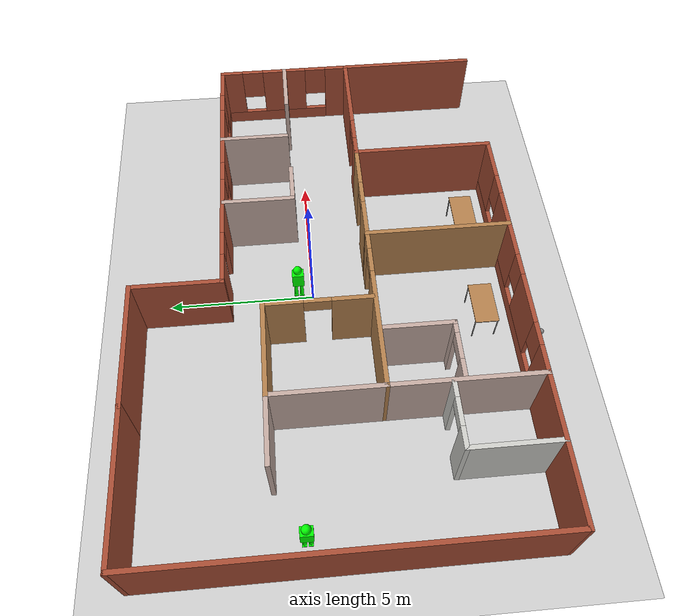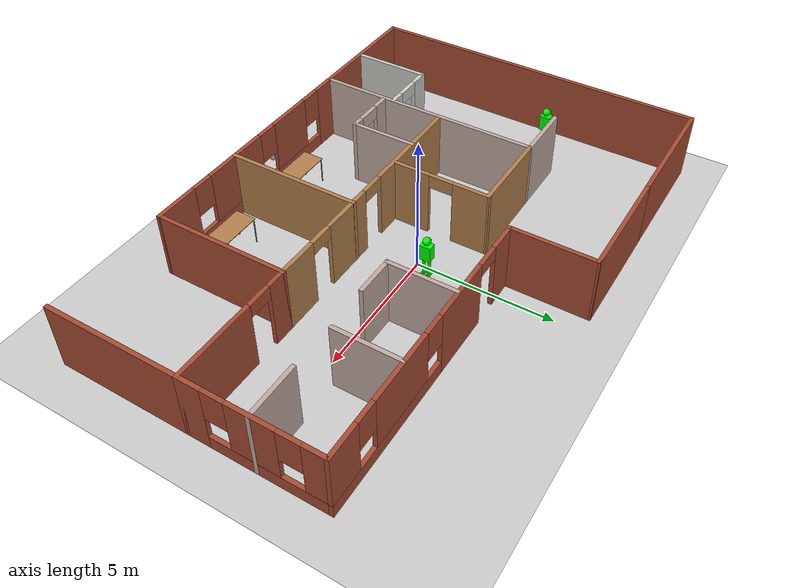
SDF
<sdf version="1.7">
 <world name="default">
  <plugin name="welcome_message" filename="libwelcome_message.so"/>
  <light name="sun" type="directional">
   <pose>0 0 10 0 -0 0</pose>
   <diffuse>0.8 0.8 0.8 1</diffuse>
   <specular>0.2 0.2 0.2 1</specular>
   <attenuation>
    <range>1000</range>
    <constant>0.9</constant>
    <linear>0.01</linear>
    <quadratic>0.001</quadratic>
   </attenuation>
   <direction>-0.5 0.1 -0.9</direction>
   <spot><inner_angle>0</inner_angle><outer_angle>0</outer_angle><falloff>0</falloff></spot>
  </light>
  <model name="ground_plane">
   <static>1</static>
   <link name="link">
    <collision name="collision">
     <geometry><plane><normal>0 0 1</normal><size>100 100</size></plane></geometry>
     <surface>
      <contact><collide_bitmask>65535</collide_bitmask></contact>
      <friction><ode><mu>100</mu><mu2>50</mu2></ode></friction>
     </surface>
    </collision>
    <visual name="visual">
     <cast_shadows>0</cast_shadows>
     <geometry><plane><normal>0 0 1</normal><size>100 100</size></plane></geometry>
     <material>
      <script><uri>file://media/materials/scripts/gazebo.material</uri><name>Gazebo/Grey</name></script>
     </material>
    </visual>
   </link>
  </model>
  <gravity>0 0 -9.8</gravity>
  <magnetic_field>6e-06 2.3e-05 -4.2e-05</magnetic_field>
  <atmosphere type="adiabatic"/>
  <physics type="ode">
   <max_step_size>0.001</max_step_size>
   <real_time_factor>1</real_time_factor>
   <real_time_update_rate>1000</real_time_update_rate>
  </physics>
  <scene><ambient>0.4 0.4 0.4 1</ambient><background>0.7 0.7 0.7 1</background><shadows>1</shadows></scene>
  <spherical_coordinates>
   <surface_model>EARTH_WGS84</surface_model>
   <latitude_deg>0</latitude_deg>
   <longitude_deg>0</longitude_deg>
   <elevation>0</elevation>
   <heading_deg>0</heading_deg>
  </spherical_coordinates>
  <model name="Building">
   <pose>-0.10758 -0.44687 0 0 -0 0</pose>
   <link name="Wall_12">
    <collision name="Wall_12_Collision">
     <geometry><box><size>4.26766 0.15 2.5</size></box></geometry>
     <pose>0 0 1.25 0 -0 0</pose>
    </collision>
    <visual name="Wall_12_Visual">
     <pose>0 0 1.25 0 -0 0</pose>
     <geometry><box><size>4.26766 0.15 2.5</size></box></geometry>
     <material>
      <script><uri>file://media/materials/scripts/gazebo.material</uri><name>Gazebo/Bricks</name></script>
      <ambient>1 1 1 1</ambient>
     </material>
     <meta><layer>0</layer></meta>
    </visual>
    <pose>-2.62625 6.34999 0 0 -0 3.14135</pose>
   </link>
   <link name="Wall_18">
    <collision name="Wall_18_Collision">
     <geometry><box><size>2.54909 0.15 2.5</size></box></geometry>
     <pose>0 0 1.25 0 -0 0</pose>
    </collision>
    <visual name="Wall_18_Visual">
     <pose>0 0 1.25 0 -0 0</pose>
     <geometry><box><size>2.54909 0.15 2.5</size></box></geometry>
     <material>
      <script><uri>file://media/materials/scripts/gazebo.material</uri><name>Gazebo/Grey</name></script>
      <ambient>0.760784 0.662745 0.627451 1</ambient>
     </material>
     <meta><layer>0</layer></meta>
    </visual>
    <pose>2.71291 2.11749 0 0 -0 -1.5708</pose>
   </link>
   <link name="Wall_19">
    <collision name="Wall_19_Collision">
     <geometry><box><size>1.5 0.15 2.5</size></box></geometry>
     <pose>0 0 1.25 0 -0 0</pose>
    </collision>
    <visual name="Wall_19_Visual">
     <pose>0 0 1.25 0 -0 0</pose>
     <geometry><box><size>1.5 0.15 2.5</size></box></geometry>
     <material>
      <script><uri>file://media/materials/scripts/gazebo.material</uri><name>Gazebo/Grey</name></script>
      <ambient>0.760784 0.662745 0.627451 1</ambient>
     </material>
     <meta><layer>0</layer></meta>
    </visual>
    <pose>3.39609 0.91795 0 0 -0 0</pose>
   </link>
   <link name="Wall_22">
    <collision name="Wall_22_Collision">
     <geometry><box><size>2 0.15 2.5</size></box></geometry>
     <pose>0 0 1.25 0 -0 0</pose>
    </collision>
    <visual name="Wall_22_Visual">
     <pose>0 0 1.25 0 -0 0</pose>
     <geometry><box><size>2 0.15 2.5</size></box></geometry>
     <material>
      <script><uri>file://media/materials/scripts/gazebo.material</uri><name>Gazebo/Grey</name></script>
      <ambient>0.760784 0.662745 0.627451 1</ambient>
     </material>
     <meta><layer>0</layer></meta>
    </visual>
    <pose>8.36008 0.923269 0 0 -0 3.14159</pose>
   </link>
   <link name="Wall_24">
    <collision name="Wall_24_Collision">
     <geometry><box><size>2.5 0.15 2.5</size></box></geometry>
     <pose>0 0 1.25 0 -0 0</pose>
    </collision>
    <visual name="Wall_24_Visual">
     <pose>0 0 1.25 0 -0 0</pose>
     <geometry><box><size>2.5 0.15 2.5</size></box></geometry>
     <material>
      <script><uri>file://media/materials/scripts/gazebo.material</uri><name>Gazebo/Grey</name></script>
      <ambient>0.760784 0.662745 0.627451 1</ambient>
     </material>
     <meta><layer>0</layer></meta>
    </visual>
    <pose>5.7297 2.18472 0 0 -0 -1.5708</pose>
   </link>
   <link name="Wall_26">
    <collision name="Wall_26_Collision">
     <geometry><box><size>3.13696 0.15 2.5</size></box></geometry>
     <pose>0 0 1.25 0 -0 0</pose>
    </collision>
    <visual name="Wall_26_Visual">
     <pose>0 0 1.25 0 -0 0</pose>
     <geometry><box><size>3.13696 0.15 2.5</size></box></geometry>
     <material>
      <script><uri>file://media/materials/scripts/gazebo.material</uri><name>Gazebo/Bricks</name></script>
      <ambient>1 1 1 1</ambient>
     </material>
     <meta><layer>0</layer></meta>
    </visual>
    <pose>-0.567427 4.85601 0 0 -0 -1.5708</pose>
   </link>
   <link name="Wall_28">
    <collision name="Wall_28_Collision">
     <geometry><box><size>3.25 0.15 2.5</size></box></geometry>
     <pose>0 0 1.25 0 -0 0</pose>
    </collision>
    <visual name="Wall_28_Visual">
     <pose>0 0 1.25 0 -0 0</pose>
     <geometry><box><size>3.25 0.15 2.5</size></box></geometry>
     <material>
      <script><uri>file://media/materials/scripts/gazebo.material</uri><name>Gazebo/Wood</name></script>
      <ambient>1 1 1 1</ambient>
     </material>
     <meta><layer>0</layer></meta>
    </visual>
    <pose>-3.11962 2.09882 0 0 -0 0</pose>
   </link>
   <link name="Wall_29">
    <pose>-1.56764 0.350671 0 0 -0 -1.56967</pose>
    <visual name="Wall_29_Visual_0">
     <pose>-1.13949 0 1.25 0 -0 0</pose>
     <geometry><box><size>1.37522 0.15 2.5</size></box></geometry>
     <material>
      <script><uri>file://media/materials/scripts/gazebo.material</uri><name>Gazebo/Wood</name></script>
      <ambient>1 1 1 1</ambient>
     </material>
     <meta><layer>0</layer></meta>
    </visual>
    <collision name="Wall_29_Collision_0">
     <geometry><box><size>1.37522 0.15 2.5</size></box></geometry>
     <pose>-1.13949 0 1.25 0 -0 0</pose>
    </collision>
    <visual name="Wall_29_Visual_1">
     <pose>1.13761 0 1.25 0 -0 0</pose>
     <geometry><box><size>1.37899 0.15 2.5</size></box></geometry>
     <material>
      <script><uri>file://media/materials/scripts/gazebo.material</uri><name>Gazebo/Wood</name></script>
      <ambient>1 1 1 1</ambient>
     </material>
     <meta><layer>0</layer></meta>
    </visual>
    <collision name="Wall_29_Collision_1">
     <geometry><box><size>1.37899 0.15 2.5</size></box></geometry>
     <pose>1.13761 0 1.25 0 -0 0</pose>
    </collision>
    <visual name="Wall_29_Visual_2">
     <pose>-0.001883 0 2.25 0 -0 0</pose>
     <geometry><box><size>0.9 0.15 0.5</size></box></geometry>
     <material>
      <script><uri>file://media/materials/scripts/gazebo.material</uri><name>Gazebo/Wood</name></script>
      <ambient>1 1 1 1</ambient>
     </material>
     <meta><layer>0</layer></meta>
    </visual>
    <collision name="Wall_29_Collision_2">
     <geometry><box><size>0.9 0.15 0.5</size></box></geometry>
     <pose>-0.001883 0 2.25 0 -0 0</pose>
    </collision>
   </link>
   <link name="Wall_3">
    <pose>9.28257 0.931014 0 0 -0 1.5708</pose>
    <visual name="Wall_3_Visual_0">
     <pose>-2.06336 0 1.25 0 -0 0</pose>
     <geometry><box><size>0.886317 0.15 2.5</size></box></geometry>
     <material>
      <script><uri>file://media/materials/scripts/gazebo.material</uri><name>Gazebo/Bricks</name></script>
      <ambient>1 1 1 1</ambient>
     </material>
     <meta><layer>0</layer></meta>
    </visual>
    <collision name="Wall_3_Collision_0">
     <geometry><box><size>0.886317 0.15 2.5</size></box></geometry>
     <pose>-2.06336 0 1.25 0 -0 0</pose>
    </collision>
    <visual name="Wall_3_Visual_1">
     <pose>0.443159 0 0.25 0 -0 0</pose>
     <geometry><box><size>4.12673 0.15 0.5</size></box></geometry>
     <material>
      <script><uri>file://media/materials/scripts/gazebo.material</uri><name>Gazebo/Bricks</name></script>
      <ambient>1 1 1 1</ambient>
     </material>
     <meta><layer>0</layer></meta>
    </visual>
    <collision name="Wall_3_Collision_1">
     <geometry><box><size>4.12673 0.15 0.5</size></box></geometry>
     <pose>0.443159 0 0.25 0 -0 0</pose>
    </collision>
    <visual name="Wall_3_Visual_2">
     <pose>0.013724 0 1.5 0 -0 0</pose>
     <geometry><box><size>1.66786 0.15 2</size></box></geometry>
     <material>
      <script><uri>file://media/materials/scripts/gazebo.material</uri><name>Gazebo/Bricks</name></script>
      <ambient>1 1 1 1</ambient>
     </material>
     <meta><layer>0</layer></meta>
    </visual>
    <collision name="Wall_3_Collision_2">
     <geometry><box><size>1.66786 0.15 2</size></box></geometry>
     <pose>0.013724 0 1.5 0 -0 0</pose>
    </collision>
    <visual name="Wall_3_Visual_3">
     <pose>2.07709 0 1.5 0 -0 0</pose>
     <geometry><box><size>0.858869 0.15 2</size></box></geometry>
     <material>
      <script><uri>file://media/materials/scripts/gazebo.material</uri><name>Gazebo/Bricks</name></script>
      <ambient>1 1 1 1</ambient>
     </material>
     <meta><layer>0</layer></meta>
    </visual>
    <collision name="Wall_3_Collision_3">
     <geometry><box><size>0.858869 0.15 2</size></box></geometry>
     <pose>2.07709 0 1.5 0 -0 0</pose>
    </collision>
    <visual name="Wall_3_Visual_4">
     <pose>-1.2202 0 1.9 0 -0 0</pose>
     <geometry><box><size>0.8 0.15 1.2</size></box></geometry>
     <material>
      <script><uri>file://media/materials/scripts/gazebo.material</uri><name>Gazebo/Bricks</name></script>
      <ambient>1 1 1 1</ambient>
     </material>
     <meta><layer>0</layer></meta>
    </visual>
    <collision name="Wall_3_Collision_4">
     <geometry><box><size>0.8 0.15 1.2</size></box></geometry>
     <pose>-1.2202 0 1.9 0 -0 0</pose>
    </collision>
    <visual name="Wall_3_Visual_5">
     <pose>1.24765 0 1.9 0 -0 0</pose>
     <geometry><box><size>0.8 0.15 1.2</size></box></geometry>
     <material>
      <script><uri>file://media/materials/scripts/gazebo.material</uri><name>Gazebo/Bricks</name></script>
      <ambient>1 1 1 1</ambient>
     </material>
     <meta><layer>0</layer></meta>
    </visual>
    <collision name="Wall_3_Collision_5">
     <geometry><box><size>0.8 0.15 1.2</size></box></geometry>
     <pose>1.24765 0 1.9 0 -0 0</pose>
    </collision>
   </link>
   <link name="Wall_31">
    <collision name="Wall_31_Collision">
     <geometry><box><size>5 0.15 2.5</size></box></geometry>
     <pose>0 0 1.25 0 -0 0</pose>
    </collision>
    <visual name="Wall_31_Visual">
     <pose>0 0 1.25 0 -0 0</pose>
     <geometry><box><size>5 0.15 2.5</size></box></geometry>
     <material>
      <script><uri>file://media/materials/scripts/gazebo.material</uri><name>Gazebo/Grey</name></script>
      <ambient>0.760784 0.662745 0.627451 1</ambient>
     </material>
     <meta><layer>0</layer></meta>
    </visual>
    <pose>-4.68508 -3.9245 0 0 -0 -1.5708</pose>
   </link>
   <link name="Wall_34">
    <collision name="Wall_34_Collision">
     <geometry><box><size>5 0.15 2.5</size></box></geometry>
     <pose>0 0 1.25 0 -0 0</pose>
    </collision>
    <visual name="Wall_34_Visual">
     <pose>0 0 1.25 0 -0 0</pose>
     <geometry><box><size>5 0.15 2.5</size></box></geometry>
     <material>
      <script><uri>file://media/materials/scripts/gazebo.material</uri><name>Gazebo/Bricks</name></script>
      <ambient>1 1 1 1</ambient>
     </material>
     <meta><layer>0</layer></meta>
    </visual>
    <pose>9.28257 -3.92551 0 0 -0 -1.5708</pose>
   </link>
   <link name="Wall_36">
    <pose>-0.001254 -6.35001 0 0 -0 -0.000107</pose>
    <visual name="Wall_36_Visual_0">
     <pose>-4.25927 0 1.25 0 -0 0</pose>
     <geometry><box><size>0.999123 0.15 2.5</size></box></geometry>
     <material>
      <script><uri>file://media/materials/scripts/gazebo.material</uri><name>Gazebo/Bricks</name></script>
      <ambient>1 1 1 1</ambient>
     </material>
     <meta><layer>0</layer></meta>
    </visual>
    <collision name="Wall_36_Collision_0">
     <geometry><box><size>0.999123 0.15 2.5</size></box></geometry>
     <pose>-4.25927 0 1.25 0 -0 0</pose>
    </collision>
    <visual name="Wall_36_Visual_1">
     <pose>0.499561 0 0.25 0 -0 0</pose>
     <geometry><box><size>8.51853 0.15 0.5</size></box></geometry>
     <material>
      <script><uri>file://media/materials/scripts/gazebo.material</uri><name>Gazebo/Bricks</name></script>
      <ambient>1 1 1 1</ambient>
     </material>
     <meta><layer>0</layer></meta>
    </visual>
    <collision name="Wall_36_Collision_1">
     <geometry><box><size>8.51853 0.15 0.5</size></box></geometry>
     <pose>0.499561 0 0.25 0 -0 0</pose>
    </collision>
    <visual name="Wall_36_Visual_2">
     <pose>-2.05731 0 1.5 0 -0 0</pose>
     <geometry><box><size>1.80478 0.15 2</size></box></geometry>
     <material>
      <script><uri>file://media/materials/scripts/gazebo.material</uri><name>Gazebo/Bricks</name></script>
      <ambient>1 1 1 1</ambient>
     </material>
     <meta><layer>0</layer></meta>
    </visual>
    <collision name="Wall_36_Collision_2">
     <geometry><box><size>1.80478 0.15 2</size></box></geometry>
     <pose>-2.05731 0 1.5 0 -0 0</pose>
    </collision>
    <visual name="Wall_36_Visual_3">
     <pose>0.968834 0 1.5 0 -0 0</pose>
     <geometry><box><size>2.64751 0.15 2</size></box></geometry>
     <material>
      <script><uri>file://media/materials/scripts/gazebo.material</uri><name>Gazebo/Bricks</name></script>
      <ambient>1 1 1 1</ambient>
     </material>
     <meta><layer>0</layer></meta>
    </visual>
    <collision name="Wall_36_Collision_3">
     <geometry><box><size>2.64751 0.15 2</size></box></geometry>
     <pose>0.968834 0 1.5 0 -0 0</pose>
    </collision>
    <visual name="Wall_36_Visual_4">
     <pose>3.92571 0 1.5 0 -0 0</pose>
     <geometry><box><size>1.66624 0.15 2</size></box></geometry>
     <material>
      <script><uri>file://media/materials/scripts/gazebo.material</uri><name>Gazebo/Bricks</name></script>
      <ambient>1 1 1 1</ambient>
     </material>
     <meta><layer>0</layer></meta>
    </visual>
    <collision name="Wall_36_Collision_4">
     <geometry><box><size>1.66624 0.15 2</size></box></geometry>
     <pose>3.92571 0 1.5 0 -0 0</pose>
    </collision>
    <visual name="Wall_36_Visual_5">
     <pose>-3.3597 0 1.9 0 -0 0</pose>
     <geometry><box><size>0.8 0.15 1.2</size></box></geometry>
     <material>
      <script><uri>file://media/materials/scripts/gazebo.material</uri><name>Gazebo/Bricks</name></script>
      <ambient>1 1 1 1</ambient>
     </material>
     <meta><layer>0</layer></meta>
    </visual>
    <collision name="Wall_36_Collision_5">
     <geometry><box><size>0.8 0.15 1.2</size></box></geometry>
     <pose>-3.3597 0 1.9 0 -0 0</pose>
    </collision>
    <visual name="Wall_36_Visual_6">
     <pose>-0.75492 0 1.9 0 -0 0</pose>
     <geometry><box><size>0.8 0.15 1.2</size></box></geometry>
     <material>
      <script><uri>file://media/materials/scripts/gazebo.material</uri><name>Gazebo/Bricks</name></script>
      <ambient>1 1 1 1</ambient>
     </material>
     <meta><layer>0</layer></meta>
    </visual>
    <collision name="Wall_36_Collision_6">
     <geometry><box><size>0.8 0.15 1.2</size></box></geometry>
     <pose>-0.75492 0 1.9 0 -0 0</pose>
    </collision>
    <visual name="Wall_36_Visual_7">
     <pose>2.69259 0 1.9 0 -0 0</pose>
     <geometry><box><size>0.8 0.15 1.2</size></box></geometry>
     <material>
      <script><uri>file://media/materials/scripts/gazebo.material</uri><name>Gazebo/Bricks</name></script>
      <ambient>1 1 1 1</ambient>
     </material>
     <meta><layer>0</layer></meta>
    </visual>
    <collision name="Wall_36_Collision_7">
     <geometry><box><size>0.8 0.15 1.2</size></box></geometry>
     <pose>2.69259 0 1.9 0 -0 0</pose>
    </collision>
   </link>
   <link name="Wall_37">
    <collision name="Wall_37_Collision">
     <geometry><box><size>5 0.15 2.5</size></box></geometry>
     <pose>0 0 1.25 0 -0 0</pose>
    </collision>
    <visual name="Wall_37_Visual">
     <pose>0 0 1.25 0 -0 0</pose>
     <geometry><box><size>5 0.15 2.5</size></box></geometry>
     <material>
      <script><uri>file://media/materials/scripts/gazebo.material</uri><name>Gazebo/Bricks</name></script>
      <ambient>1 1 1 1</ambient>
     </material>
     <meta><layer>0</layer></meta>
    </visual>
    <pose>4.68257 -3.92551 0 0 -0 1.5708</pose>
   </link>
   <link name="Wall_39">
    <collision name="Wall_39_Collision">
     <geometry><box><size>5 0.15 2.5</size></box></geometry>
     <pose>0 0 1.25 0 -0 0</pose>
    </collision>
    <visual name="Wall_39_Visual">
     <pose>0 0 1.25 0 -0 0</pose>
     <geometry><box><size>5 0.15 2.5</size></box></geometry>
     <material>
      <script><uri>file://media/materials/scripts/gazebo.material</uri><name>Gazebo/Wood</name></script>
      <ambient>1 1 1 1</ambient>
     </material>
     <meta><layer>0</layer></meta>
    </visual>
    <pose>0.958073 -3.91802 0 0 -0 -1.5708</pose>
   </link>
   <link name="Wall_41">
    <collision name="Wall_41_Collision">
     <geometry><box><size>4.75 0.15 2.5</size></box></geometry>
     <pose>0 0 1.25 0 -0 0</pose>
    </collision>
    <visual name="Wall_41_Visual">
     <pose>0 0 1.25 0 -0 0</pose>
     <geometry><box><size>4.75 0.15 2.5</size></box></geometry>
     <material>
      <script><uri>file://media/materials/scripts/gazebo.material</uri><name>Gazebo/Bricks</name></script>
      <ambient>1 1 1 1</ambient>
     </material>
     <meta><layer>0</layer></meta>
    </visual>
    <pose>-6.98508 6.34587 0 0 -0 3.14159</pose>
   </link>
   <link name="Wall_42">
    <collision name="Wall_42_Collision">
     <geometry><box><size>12.75 0.15 2.5</size></box></geometry>
     <pose>0 0 1.25 0 -0 0</pose>
    </collision>
    <visual name="Wall_42_Visual">
     <pose>0 0 1.25 0 -0 0</pose>
     <geometry><box><size>12.75 0.15 2.5</size></box></geometry>
     <material>
      <script><uri>file://media/materials/scripts/gazebo.material</uri><name>Gazebo/Bricks</name></script>
      <ambient>1 1 1 1</ambient>
     </material>
     <meta><layer>0</layer></meta>
    </visual>
    <pose>-9.28508 0.045872 0 0 -0 -1.5708</pose>
   </link>
   <link name="Wall_44">
    <collision name="Wall_44_Collision">
     <geometry><box><size>4.75 0.15 2.5</size></box></geometry>
     <pose>0 0 1.25 0 -0 0</pose>
    </collision>
    <visual name="Wall_44_Visual">
     <pose>0 0 1.25 0 -0 0</pose>
     <geometry><box><size>4.75 0.15 2.5</size></box></geometry>
     <material>
      <script><uri>file://media/materials/scripts/gazebo.material</uri><name>Gazebo/Bricks</name></script>
      <ambient>1 1 1 1</ambient>
     </material>
     <meta><layer>0</layer></meta>
    </visual>
    <pose>-6.98508 -6.3495 0 0 -0 3.14159</pose>
   </link>
   <link name="Wall_47">
    <collision name="Wall_47_Collision">
     <geometry><box><size>3.75 0.15 2.5</size></box></geometry>
     <pose>0 0 1.25 0 -0 0</pose>
    </collision>
    <visual name="Wall_47_Visual">
     <pose>0 0 1.25 0 -0 0</pose>
     <geometry><box><size>3.75 0.15 2.5</size></box></geometry>
     <material>
      <script><uri>file://media/materials/scripts/gazebo.material</uri><name>Gazebo/Grey</name></script>
      <ambient>0.760784 0.662745 0.627451 1</ambient>
     </material>
     <meta><layer>0</layer></meta>
    </visual>
    <pose>-4.68508 0.300498 0 0 -0 1.5708</pose>
   </link>
   <link name="Wall_5">
    <pose>4.35757 3.36254 0 0 -0 0</pose>
    <visual name="Wall_5_Visual_0">
     <pose>-4.43313 0 1.25 0 -0 0</pose>
     <geometry><box><size>1.13374 0.15 2.5</size></box></geometry>
     <material>
      <script><uri>file://media/materials/scripts/gazebo.material</uri><name>Gazebo/Bricks</name></script>
      <ambient>1 1 1 1</ambient>
     </material>
     <meta><layer>0</layer></meta>
    </visual>
    <collision name="Wall_5_Collision_0">
     <geometry><box><size>1.13374 0.15 2.5</size></box></geometry>
     <pose>-4.43313 0 1.25 0 -0 0</pose>
    </collision>
    <visual name="Wall_5_Visual_1">
     <pose>-1.77928 0 1.25 0 -0 0</pose>
     <geometry><box><size>2.37396 0.15 2.5</size></box></geometry>
     <material>
      <script><uri>file://media/materials/scripts/gazebo.material</uri><name>Gazebo/Bricks</name></script>
      <ambient>1 1 1 1</ambient>
     </material>
     <meta><layer>0</layer></meta>
    </visual>
    <collision name="Wall_5_Collision_1">
     <geometry><box><size>2.37396 0.15 2.5</size></box></geometry>
     <pose>-1.77928 0 1.25 0 -0 0</pose>
    </collision>
    <visual name="Wall_5_Visual_2">
     <pose>2.20385 0 0.25 0 -0 0</pose>
     <geometry><box><size>5.5923 0.15 0.5</size></box></geometry>
     <material>
      <script><uri>file://media/materials/scripts/gazebo.material</uri><name>Gazebo/Bricks</name></script>
      <ambient>1 1 1 1</ambient>
     </material>
     <meta><layer>0</layer></meta>
    </visual>
    <collision name="Wall_5_Collision_2">
     <geometry><box><size>5.5923 0.15 0.5</size></box></geometry>
     <pose>2.20385 0 0.25 0 -0 0</pose>
    </collision>
    <visual name="Wall_5_Visual_3">
     <pose>1.54973 0 1.5 0 -0 0</pose>
     <geometry><box><size>2.68406 0.15 2</size></box></geometry>
     <material>
      <script><uri>file://media/materials/scripts/gazebo.material</uri><name>Gazebo/Bricks</name></script>
      <ambient>1 1 1 1</ambient>
     </material>
     <meta><layer>0</layer></meta>
    </visual>
    <collision name="Wall_5_Collision_3">
     <geometry><box><size>2.68406 0.15 2</size></box></geometry>
     <pose>1.54973 0 1.5 0 -0 0</pose>
    </collision>
    <visual name="Wall_5_Visual_4">
     <pose>4.34588 0 1.5 0 -0 0</pose>
     <geometry><box><size>1.30824 0.15 2</size></box></geometry>
     <material>
      <script><uri>file://media/materials/scripts/gazebo.material</uri><name>Gazebo/Bricks</name></script>
      <ambient>1 1 1 1</ambient>
     </material>
     <meta><layer>0</layer></meta>
    </visual>
    <collision name="Wall_5_Collision_4">
     <geometry><box><size>1.30824 0.15 2</size></box></geometry>
     <pose>4.34588 0 1.5 0 -0 0</pose>
    </collision>
    <visual name="Wall_5_Visual_5">
     <pose>-0.1923 0 1.9 0 -0 0</pose>
     <geometry><box><size>0.8 0.15 1.2</size></box></geometry>
     <material>
      <script><uri>file://media/materials/scripts/gazebo.material</uri><name>Gazebo/Bricks</name></script>
      <ambient>1 1 1 1</ambient>
     </material>
     <meta><layer>0</layer></meta>
    </visual>
    <collision name="Wall_5_Collision_5">
     <geometry><box><size>0.8 0.15 1.2</size></box></geometry>
     <pose>-0.1923 0 1.9 0 -0 0</pose>
    </collision>
    <visual name="Wall_5_Visual_6">
     <pose>3.29176 0 1.9 0 -0 0</pose>
     <geometry><box><size>0.8 0.15 1.2</size></box></geometry>
     <material>
      <script><uri>file://media/materials/scripts/gazebo.material</uri><name>Gazebo/Bricks</name></script>
      <ambient>1 1 1 1</ambient>
     </material>
     <meta><layer>0</layer></meta>
    </visual>
    <collision name="Wall_5_Collision_6">
     <geometry><box><size>0.8 0.15 1.2</size></box></geometry>
     <pose>3.29176 0 1.9 0 -0 0</pose>
    </collision>
    <visual name="Wall_5_Visual_7">
     <pose>-3.41626 0 2.25 0 -0 0</pose>
     <geometry><box><size>0.9 0.15 0.5</size></box></geometry>
     <material>
      <script><uri>file://media/materials/scripts/gazebo.material</uri><name>Gazebo/Bricks</name></script>
      <ambient>1 1 1 1</ambient>
     </material>
     <meta><layer>0</layer></meta>
    </visual>
    <collision name="Wall_5_Collision_7">
     <geometry><box><size>0.9 0.15 0.5</size></box></geometry>
     <pose>-3.41626 0 2.25 0 -0 0</pose>
    </collision>
   </link>
   <link name="Wall_51">
    <pose>-5.74884 -3.48761 0 0 -0 3.14159</pose>
    <visual name="Wall_51_Visual_0">
     <pose>-0.814565 0 1.25 0 -0 0</pose>
     <geometry><box><size>0.62087 0.15 2.5</size></box></geometry>
     <material>
      <script><uri>file://media/materials/scripts/gazebo.material</uri><name>Gazebo/CeilingTiled</name></script>
      <ambient>0.760784 0.662745 0.627451 1</ambient>
     </material>
     <meta><layer>0</layer></meta>
    </visual>
    <collision name="Wall_51_Collision_0">
     <geometry><box><size>0.62087 0.15 2.5</size></box></geometry>
     <pose>-0.814565 0 1.25 0 -0 0</pose>
    </collision>
    <visual name="Wall_51_Visual_1">
     <pose>0.760435 0 1.25 0 -0 0</pose>
     <geometry><box><size>0.72913 0.15 2.5</size></box></geometry>
     <material>
      <script><uri>file://media/materials/scripts/gazebo.material</uri><name>Gazebo/CeilingTiled</name></script>
      <ambient>0.760784 0.662745 0.627451 1</ambient>
     </material>
     <meta><layer>0</layer></meta>
    </visual>
    <collision name="Wall_51_Collision_1">
     <geometry><box><size>0.72913 0.15 2.5</size></box></geometry>
     <pose>0.760435 0 1.25 0 -0 0</pose>
    </collision>
    <visual name="Wall_51_Visual_2">
     <pose>-0.05413 0 2.25 0 -0 0</pose>
     <geometry><box><size>0.9 0.15 0.5</size></box></geometry>
     <material>
      <script><uri>file://media/materials/scripts/gazebo.material</uri><name>Gazebo/CeilingTiled</name></script>
      <ambient>0.760784 0.662745 0.627451 1</ambient>
     </material>
     <meta><layer>0</layer></meta>
    </visual>
    <collision name="Wall_51_Collision_2">
     <geometry><box><size>0.9 0.15 0.5</size></box></geometry>
     <pose>-0.05413 0 2.25 0 -0 0</pose>
    </collision>
   </link>
   <link name="Wall_52">
    <collision name="Wall_52_Collision">
     <geometry><box><size>3 0.15 2.5</size></box></geometry>
     <pose>0 0 1.25 0 -0 0</pose>
    </collision>
    <visual name="Wall_52_Visual">
     <pose>0 0 1.25 0 -0 0</pose>
     <geometry><box><size>3 0.15 2.5</size></box></geometry>
     <material>
      <script><uri>file://media/materials/scripts/gazebo.material</uri><name>Gazebo/CeilingTiled</name></script>
      <ambient>0.760784 0.662745 0.627451 1</ambient>
     </material>
     <meta><layer>0</layer></meta>
    </visual>
    <pose>-6.79884 -4.91261 0 0 -0 -1.5708</pose>
   </link>
   <link name="Wall_54">
    <collision name="Wall_54_Collision">
     <geometry><box><size>2.5 0.15 2.5</size></box></geometry>
     <pose>0 0 1.25 0 -0 0</pose>
    </collision>
    <visual name="Wall_54_Visual">
     <pose>0 0 1.25 0 -0 0</pose>
     <geometry><box><size>2.5 0.15 2.5</size></box></geometry>
     <material>
      <script><uri>file://media/materials/scripts/gazebo.material</uri><name>Gazebo/Grey</name></script>
      <ambient>0.760784 0.662745 0.627451 1</ambient>
     </material>
     <meta><layer>0</layer></meta>
    </visual>
    <pose>-2.72782 -2.67582 0 0 -0 -1.5708</pose>
   </link>
   <link name="Wall_55">
    <pose>-3.65282 -3.85082 0 0 -0 3.14159</pose>
    <visual name="Wall_55_Visual_0">
     <pose>-0.769257 0 1.25 0 -0 0</pose>
     <geometry><box><size>0.461487 0.15 2.5</size></box></geometry>
     <material>
      <script><uri>file://media/materials/scripts/gazebo.material</uri><name>Gazebo/Grey</name></script>
      <ambient>0.760784 0.662745 0.627451 1</ambient>
     </material>
     <meta><layer>0</layer></meta>
    </visual>
    <collision name="Wall_55_Collision_0">
     <geometry><box><size>0.461487 0.15 2.5</size></box></geometry>
     <pose>-0.769257 0 1.25 0 -0 0</pose>
    </collision>
    <visual name="Wall_55_Visual_1">
     <pose>0.680743 0 1.25 0 -0 0</pose>
     <geometry><box><size>0.638513 0.15 2.5</size></box></geometry>
     <material>
      <script><uri>file://media/materials/scripts/gazebo.material</uri><name>Gazebo/Grey</name></script>
      <ambient>0.760784 0.662745 0.627451 1</ambient>
     </material>
     <meta><layer>0</layer></meta>
    </visual>
    <collision name="Wall_55_Collision_1">
     <geometry><box><size>0.638513 0.15 2.5</size></box></geometry>
     <pose>0.680743 0 1.25 0 -0 0</pose>
    </collision>
    <visual name="Wall_55_Visual_2">
     <pose>-0.088513 0 2.25 0 -0 0</pose>
     <geometry><box><size>0.9 0.15 0.5</size></box></geometry>
     <material>
      <script><uri>file://media/materials/scripts/gazebo.material</uri><name>Gazebo/Grey</name></script>
      <ambient>0.760784 0.662745 0.627451 1</ambient>
     </material>
     <meta><layer>0</layer></meta>
    </visual>
    <collision name="Wall_55_Collision_2">
     <geometry><box><size>0.9 0.15 0.5</size></box></geometry>
     <pose>-0.088513 0 2.25 0 -0 0</pose>
    </collision>
   </link>
   <link name="Wall_57">
    <pose>-0.001254 -1.50001 0 0 -0 3.14148</pose>
    <visual name="Wall_57_Visual_0">
     <pose>-3.98961 0 1.25 0 -0 0</pose>
     <geometry><box><size>1.53844 0.15 2.5</size></box></geometry>
     <material>
      <script><uri>file://media/materials/scripts/gazebo.material</uri><name>Gazebo/Wood</name></script>
      <ambient>1 1 1 1</ambient>
     </material>
     <meta><layer>0</layer></meta>
    </visual>
    <collision name="Wall_57_Collision_0">
     <geometry><box><size>1.53844 0.15 2.5</size></box></geometry>
     <pose>-3.98961 0 1.25 0 -0 0</pose>
    </collision>
    <visual name="Wall_57_Visual_1">
     <pose>-1.31362 0 1.25 0 -0 0</pose>
     <geometry><box><size>2.01352 0.15 2.5</size></box></geometry>
     <material>
      <script><uri>file://media/materials/scripts/gazebo.material</uri><name>Gazebo/Wood</name></script>
      <ambient>1 1 1 1</ambient>
     </material>
     <meta><layer>0</layer></meta>
    </visual>
    <collision name="Wall_57_Collision_1">
     <geometry><box><size>2.01352 0.15 2.5</size></box></geometry>
     <pose>-1.31362 0 1.25 0 -0 0</pose>
    </collision>
    <visual name="Wall_57_Visual_2">
     <pose>2.67598 0 1.25 0 -0 0</pose>
     <geometry><box><size>4.16569 0.15 2.5</size></box></geometry>
     <material>
      <script><uri>file://media/materials/scripts/gazebo.material</uri><name>Gazebo/Wood</name></script>
      <ambient>1 1 1 1</ambient>
     </material>
     <meta><layer>0</layer></meta>
    </visual>
    <collision name="Wall_57_Collision_2">
     <geometry><box><size>4.16569 0.15 2.5</size></box></geometry>
     <pose>2.67598 0 1.25 0 -0 0</pose>
    </collision>
    <visual name="Wall_57_Visual_3">
     <pose>-2.77038 0 2.25 0 -0 0</pose>
     <geometry><box><size>0.9 0.15 0.5</size></box></geometry>
     <material>
      <script><uri>file://media/materials/scripts/gazebo.material</uri><name>Gazebo/Wood</name></script>
      <ambient>1 1 1 1</ambient>
     </material>
     <meta><layer>0</layer></meta>
    </visual>
    <collision name="Wall_57_Collision_3">
     <geometry><box><size>0.9 0.15 0.5</size></box></geometry>
     <pose>-2.77038 0 2.25 0 -0 0</pose>
    </collision>
    <visual name="Wall_57_Visual_4">
     <pose>0.143136 0 2.25 0 -0 0</pose>
     <geometry><box><size>0.9 0.15 0.5</size></box></geometry>
     <material>
      <script><uri>file://media/materials/scripts/gazebo.material</uri><name>Gazebo/Wood</name></script>
      <ambient>1 1 1 1</ambient>
     </material>
     <meta><layer>0</layer></meta>
    </visual>
    <collision name="Wall_57_Collision_4">
     <geometry><box><size>0.9 0.15 0.5</size></box></geometry>
     <pose>0.143136 0 2.25 0 -0 0</pose>
    </collision>
   </link>
   <link name="Wall_59">
    <pose>6.98257 -1.50051 0 0 -0 0</pose>
    <visual name="Wall_59_Visual_0">
     <pose>-1.98813 0 1.25 0 -0 0</pose>
     <geometry><box><size>0.773745 0.15 2.5</size></box></geometry>
     <material>
      <script><uri>file://media/materials/scripts/gazebo.material</uri><name>Gazebo/Bricks</name></script>
      <ambient>1 1 1 1</ambient>
     </material>
     <meta><layer>0</layer></meta>
    </visual>
    <collision name="Wall_59_Collision_0">
     <geometry><box><size>0.773745 0.15 2.5</size></box></geometry>
     <pose>-1.98813 0 1.25 0 -0 0</pose>
    </collision>
    <visual name="Wall_59_Visual_1">
     <pose>0.836872 0 1.25 0 -0 0</pose>
     <geometry><box><size>3.07626 0.15 2.5</size></box></geometry>
     <material>
      <script><uri>file://media/materials/scripts/gazebo.material</uri><name>Gazebo/Bricks</name></script>
      <ambient>1 1 1 1</ambient>
     </material>
     <meta><layer>0</layer></meta>
    </visual>
    <collision name="Wall_59_Collision_1">
     <geometry><box><size>3.07626 0.15 2.5</size></box></geometry>
     <pose>0.836872 0 1.25 0 -0 0</pose>
    </collision>
    <visual name="Wall_59_Visual_2">
     <pose>-1.15125 0 2.25 0 -0 0</pose>
     <geometry><box><size>0.9 0.15 0.5</size></box></geometry>
     <material>
      <script><uri>file://media/materials/scripts/gazebo.material</uri><name>Gazebo/Bricks</name></script>
      <ambient>1 1 1 1</ambient>
     </material>
     <meta><layer>0</layer></meta>
    </visual>
    <collision name="Wall_59_Collision_2">
     <geometry><box><size>0.9 0.15 0.5</size></box></geometry>
     <pose>-1.15125 0 2.25 0 -0 0</pose>
    </collision>
   </link>
   <link name="Wall_61">
    <collision name="Wall_61_Collision">
     <geometry><box><size>2.25 0.15 2.5</size></box></geometry>
     <pose>0 0 1.25 0 -0 0</pose>
    </collision>
    <visual name="Wall_61_Visual">
     <pose>0 0 1.25 0 -0 0</pose>
     <geometry><box><size>2.25 0.15 2.5</size></box></geometry>
     <material>
      <script><uri>file://media/materials/scripts/gazebo.material</uri><name>Gazebo/Grey</name></script>
      <ambient>0.760784 0.662745 0.627451 1</ambient>
     </material>
     <meta><layer>0</layer></meta>
    </visual>
    <pose>-5.73508 2.1005 0 0 -0 3.14159</pose>
   </link>
   <static>1</static>
  </model>
  <model name="HumanoidRobot">
   <link name="link_1">
    <inertial>
     <mass>1</mass>
     <inertia>
      <ixx>0.166667</ixx>
      <ixy>0</ixy>
      <ixz>0</ixz>
      <iyy>0.166667</iyy>
      <iyz>0</iyz>
      <izz>0.166667</izz>
     </inertia>
    </inertial>
    <pose>0 -0.000833 0.458333 0 -0 0</pose>
    <visual name="visual">
     <geometry><box><size>0.3 0.4 0.6</size></box></geometry>
     <material>
      <lighting>1</lighting>
      <script><uri>file://media/materials/scripts/gazebo.material</uri><name>Gazebo/Grey</name></script>
      <shader type="pixel"><normal_map>__default__</normal_map></shader>
      <ambient>0 1 0 1</ambient>
      <diffuse>0.7 0.7 0.7 1</diffuse>
      <specular>0.01 0.01 0.01 1</specular>
      <emissive>0 0 0 1</emissive>
     </material>
    </visual>
    <collision name="collision">
     <geometry><box><size>0.3 0.4 0.6</size></box></geometry>
     <surface>
      <friction>
       <ode><mu>1</mu><mu2>1</mu2><fdir1>0 0 0</fdir1><slip1>0</slip1><slip2>0</slip2></ode>
       <torsional>
        <coefficient>1</coefficient>
        <patch_radius>0</patch_radius>
        <surface_radius>0</surface_radius>
        <use_patch_radius>1</use_patch_radius>
        <ode><slip>0</slip></ode>
       </torsional>
      </friction>
      <bounce><restitution_coefficient>0</restitution_coefficient><threshold>1e+06</threshold></bounce>
      <contact>
       <collide_without_contact>0</collide_without_contact>
       <collide_without_contact_bitmask>1</collide_without_contact_bitmask>
       <collide_bitmask>1</collide_bitmask>
       <ode>
        <soft_cfm>0</soft_cfm>
        <soft_erp>0.2</soft_erp>
        <kp>1e+13</kp>
        <kd>1</kd>
        <max_vel>0.01</max_vel>
        <min_depth>0</min_depth>
       </ode>
       <bullet>
        <split_impulse>1</split_impulse>
        <split_impulse_penetration_threshold>-0.01</split_impulse_penetration_threshold>
        <soft_cfm>0</soft_cfm>
        <soft_erp>0.2</soft_erp>
        <kp>1e+13</kp>
        <kd>1</kd>
       </bullet>
      </contact>
     </surface>
    </collision>
   </link>
   <link name="link_2">
    <inertial>
     <mass>1</mass>
     <inertia><ixx>0.145833</ixx><ixy>0</ixy><ixz>0</ixz><iyy>0.145833</iyy><iyz>0</iyz><izz>0.125</izz></inertia>
    </inertial>
    <pose>0 -0.100833 -0.166667 0 -0 0</pose>
    <visual name="visual">
     <geometry><cylinder><radius>0.06</radius><length>0.65</length></cylinder></geometry>
     <material>
      <lighting>1</lighting>
      <script><uri>file://media/materials/scripts/gazebo.material</uri><name>Gazebo/Grey</name></script>
      <shader type="pixel"><normal_map>__default__</normal_map></shader>
      <ambient>0 1 0 1</ambient>
      <diffuse>0.7 0.7 0.7 1</diffuse>
      <specular>0.01 0.01 0.01 1</specular>
      <emissive>0 0 0 1</emissive>
     </material>
    </visual>
    <collision name="collision">
     <geometry><cylinder><radius>0.06</radius><length>0.65</length></cylinder></geometry>
     <surface>
      <friction>
       <ode><mu>1</mu><mu2>1</mu2><fdir1>0 0 0</fdir1><slip1>0</slip1><slip2>0</slip2></ode>
       <torsional>
        <coefficient>1</coefficient>
        <patch_radius>0</patch_radius>
        <surface_radius>0</surface_radius>
        <use_patch_radius>1</use_patch_radius>
        <ode><slip>0</slip></ode>
       </torsional>
      </friction>
      <bounce><restitution_coefficient>0</restitution_coefficient><threshold>1e+06</threshold></bounce>
      <contact>
       <collide_without_contact>0</collide_without_contact>
       <collide_without_contact_bitmask>1</collide_without_contact_bitmask>
       <collide_bitmask>1</collide_bitmask>
       <ode>
        <soft_cfm>0</soft_cfm>
        <soft_erp>0.2</soft_erp>
        <kp>1e+13</kp>
        <kd>1</kd>
        <max_vel>0.01</max_vel>
        <min_depth>0</min_depth>
       </ode>
       <bullet>
        <split_impulse>1</split_impulse>
        <split_impulse_penetration_threshold>-0.01</split_impulse_penetration_threshold>
        <soft_cfm>0</soft_cfm>
        <soft_erp>0.2</soft_erp>
        <kp>1e+13</kp>
        <kd>1</kd>
       </bullet>
      </contact>
     </surface>
    </collision>
   </link>
   <link name="link_2_clone">
    <inertial>
     <mass>1</mass>
     <inertia><ixx>0.145833</ixx><ixy>0</ixy><ixz>0</ixz><iyy>0.145833</iyy><iyz>0</iyz><izz>0.125</izz></inertia>
    </inertial>
    <pose>0 0.099167 -0.166667 0 -0 0</pose>
    <visual name="visual">
     <geometry><cylinder><radius>0.06</radius><length>0.65</length></cylinder></geometry>
     <material>
      <lighting>1</lighting>
      <script><uri>file://media/materials/scripts/gazebo.material</uri><name>Gazebo/Grey</name></script>
      <shader type="pixel"><normal_map>__default__</normal_map></shader>
      <ambient>0 1 0 1</ambient>
      <diffuse>0.7 0.7 0.7 1</diffuse>
      <specular>0.01 0.01 0.01 1</specular>
      <emissive>0 0 0 1</emissive>
     </material>
    </visual>
    <collision name="collision">
     <geometry><cylinder><radius>0.06</radius><length>0.65</length></cylinder></geometry>
     <surface>
      <friction>
       <ode><mu>1</mu><mu2>1</mu2><fdir1>0 0 0</fdir1><slip1>0</slip1><slip2>0</slip2></ode>
       <torsional>
        <coefficient>1</coefficient>
        <patch_radius>0</patch_radius>
        <surface_radius>0</surface_radius>
        <use_patch_radius>1</use_patch_radius>
        <ode><slip>0</slip></ode>
       </torsional>
      </friction>
      <bounce><restitution_coefficient>0</restitution_coefficient><threshold>1e+06</threshold></bounce>
      <contact>
       <collide_without_contact>0</collide_without_contact>
       <collide_without_contact_bitmask>1</collide_without_contact_bitmask>
       <collide_bitmask>1</collide_bitmask>
       <ode>
        <soft_cfm>0</soft_cfm>
        <soft_erp>0.2</soft_erp>
        <kp>1e+13</kp>
        <kd>1</kd>
        <max_vel>0.01</max_vel>
        <min_depth>0</min_depth>
       </ode>
       <bullet>
        <split_impulse>1</split_impulse>
        <split_impulse_penetration_threshold>-0.01</split_impulse_penetration_threshold>
        <soft_cfm>0</soft_cfm>
        <soft_erp>0.2</soft_erp>
        <kp>1e+13</kp>
        <kd>1</kd>
       </bullet>
      </contact>
     </surface>
    </collision>
   </link>
   <link name="link_3">
    <inertial>
     <mass>1</mass>
     <inertia>
      <ixx>0.166667</ixx>
      <ixy>0</ixy>
      <ixz>0</ixz>
      <iyy>0.166667</iyy>
      <iyz>0</iyz>
      <izz>0.166667</izz>
     </inertia>
    </inertial>
    <pose>0 -0.095833 -0.516667 0 -0 0</pose>
    <visual name="visual">
     <geometry><box><size>0.2 0.14 0.05</size></box></geometry>
     <material>
      <lighting>1</lighting>
      <script><uri>file://media/materials/scripts/gazebo.material</uri><name>Gazebo/Grey</name></script>
      <shader type="pixel"><normal_map>__default__</normal_map></shader>
      <ambient>0 1 0 1</ambient>
      <diffuse>0.7 0.7 0.7 1</diffuse>
      <specular>0.01 0.01 0.01 1</specular>
      <emissive>0 0 0 1</emissive>
     </material>
    </visual>
    <collision name="collision">
     <geometry><box><size>0.2 0.14 0.05</size></box></geometry>
     <surface>
      <friction>
       <ode><mu>1</mu><mu2>1</mu2><fdir1>0 0 0</fdir1><slip1>0</slip1><slip2>0</slip2></ode>
       <torsional>
        <coefficient>1</coefficient>
        <patch_radius>0</patch_radius>
        <surface_radius>0</surface_radius>
        <use_patch_radius>1</use_patch_radius>
        <ode><slip>0</slip></ode>
       </torsional>
      </friction>
      <bounce><restitution_coefficient>0</restitution_coefficient><threshold>1e+06</threshold></bounce>
      <contact>
       <collide_without_contact>0</collide_without_contact>
       <collide_without_contact_bitmask>1</collide_without_contact_bitmask>
       <collide_bitmask>1</collide_bitmask>
       <ode>
        <soft_cfm>0</soft_cfm>
        <soft_erp>0.2</soft_erp>
        <kp>1e+13</kp>
        <kd>1</kd>
        <max_vel>0.01</max_vel>
        <min_depth>0</min_depth>
       </ode>
       <bullet>
        <split_impulse>1</split_impulse>
        <split_impulse_penetration_threshold>-0.01</split_impulse_penetration_threshold>
        <soft_cfm>0</soft_cfm>
        <soft_erp>0.2</soft_erp>
        <kp>1e+13</kp>
        <kd>1</kd>
       </bullet>
      </contact>
     </surface>
    </collision>
   </link>
   <link name="link_3_clone">
    <inertial>
     <mass>1</mass>
     <inertia>
      <ixx>0.166667</ixx>
      <ixy>0</ixy>
      <ixz>0</ixz>
      <iyy>0.166667</iyy>
      <iyz>0</iyz>
      <izz>0.166667</izz>
     </inertia>
    </inertial>
    <pose>0 0.099167 -0.516667 0 -0 0</pose>
    <visual name="visual">
     <geometry><box><size>0.2 0.14 0.05</size></box></geometry>
     <material>
      <lighting>1</lighting>
      <script><uri>file://media/materials/scripts/gazebo.material</uri><name>Gazebo/Grey</name></script>
      <shader type="pixel"><normal_map>__default__</normal_map></shader>
      <ambient>0 1 0 1</ambient>
      <diffuse>0.7 0.7 0.7 1</diffuse>
      <specular>0.01 0.01 0.01 1</specular>
      <emissive>0 0 0 1</emissive>
     </material>
    </visual>
    <collision name="collision">
     <geometry><box><size>0.2 0.14 0.05</size></box></geometry>
     <surface>
      <friction>
       <ode><mu>1</mu><mu2>1</mu2><fdir1>0 0 0</fdir1><slip1>0</slip1><slip2>0</slip2></ode>
       <torsional>
        <coefficient>1</coefficient>
        <patch_radius>0</patch_radius>
        <surface_radius>0</surface_radius>
        <use_patch_radius>1</use_patch_radius>
        <ode><slip>0</slip></ode>
       </torsional>
      </friction>
      <bounce><restitution_coefficient>0</restitution_coefficient><threshold>1e+06</threshold></bounce>
      <contact>
       <collide_without_contact>0</collide_without_contact>
       <collide_without_contact_bitmask>1</collide_without_contact_bitmask>
       <collide_bitmask>1</collide_bitmask>
       <ode>
        <soft_cfm>0</soft_cfm>
        <soft_erp>0.2</soft_erp>
        <kp>1e+13</kp>
        <kd>1</kd>
        <max_vel>0.01</max_vel>
        <min_depth>0</min_depth>
       </ode>
       <bullet>
        <split_impulse>1</split_impulse>
        <split_impulse_penetration_threshold>-0.01</split_impulse_penetration_threshold>
        <soft_cfm>0</soft_cfm>
        <soft_erp>0.2</soft_erp>
        <kp>1e+13</kp>
        <kd>1</kd>
       </bullet>
      </contact>
     </surface>
    </collision>
   </link>
   <link name="link_4">
    <inertial>
     <mass>1</mass>
     <inertia><ixx>0.1</ixx><ixy>0</ixy><ixz>0</ixz><iyy>0.1</iyy><iyz>0</iyz><izz>0.1</izz></inertia>
    </inertial>
    <pose>0 -0.000833 0.908333 0 -0 0</pose>
    <visual name="visual">
     <geometry><sphere><radius>0.15</radius></sphere></geometry>
     <material>
      <lighting>1</lighting>
      <script><uri>file://media/materials/scripts/gazebo.material</uri><name>Gazebo/Grey</name></script>
      <shader type="pixel"><normal_map>__default__</normal_map></shader>
      <ambient>0 1 0 1</ambient>
      <diffuse>0.7 0.7 0.7 1</diffuse>
      <specular>0.01 0.01 0.01 1</specular>
      <emissive>0 0 0 1</emissive>
     </material>
    </visual>
    <collision name="collision">
     <geometry><sphere><radius>0.15</radius></sphere></geometry>
     <surface>
      <friction>
       <ode><mu>1</mu><mu2>1</mu2><fdir1>0 0 0</fdir1><slip1>0</slip1><slip2>0</slip2></ode>
       <torsional>
        <coefficient>1</coefficient>
        <patch_radius>0</patch_radius>
        <surface_radius>0</surface_radius>
        <use_patch_radius>1</use_patch_radius>
        <ode><slip>0</slip></ode>
       </torsional>
      </friction>
      <bounce><restitution_coefficient>0</restitution_coefficient><threshold>1e+06</threshold></bounce>
      <contact>
       <collide_without_contact>0</collide_without_contact>
       <collide_without_contact_bitmask>1</collide_without_contact_bitmask>
       <collide_bitmask>1</collide_bitmask>
       <ode>
        <soft_cfm>0</soft_cfm>
        <soft_erp>0.2</soft_erp>
        <kp>1e+13</kp>
        <kd>1</kd>
        <max_vel>0.01</max_vel>
        <min_depth>0</min_depth>
       </ode>
       <bullet>
        <split_impulse>1</split_impulse>
        <split_impulse_penetration_threshold>-0.01</split_impulse_penetration_threshold>
        <soft_cfm>0</soft_cfm>
        <soft_erp>0.2</soft_erp>
        <kp>1e+13</kp>
        <kd>1</kd>
       </bullet>
      </contact>
     </surface>
    </collision>
   </link>
   <joint name="link_1_JOINT_1" type="fixed">
    <parent>link_1</parent>
    <child>link_2</child>
    <physics>
     <ode><limit><cfm>0</cfm><erp>0.2</erp></limit><suspension><cfm>0</cfm><erp>0.2</erp></suspension></ode>
    </physics>
   </joint>
   <joint name="link_1_JOINT_2" type="fixed">
    <parent>link_1</parent>
    <child>link_2_clone</child>
    <physics>
     <ode><limit><cfm>0</cfm><erp>0.2</erp></limit><suspension><cfm>0</cfm><erp>0.2</erp></suspension></ode>
    </physics>
   </joint>
   <joint name="link_1_JOINT_7" type="fixed">
    <parent>link_1</parent>
    <child>link_4</child>
    <physics>
     <ode><limit><cfm>0</cfm><erp>0.2</erp></limit><suspension><cfm>0</cfm><erp>0.2</erp></suspension></ode>
    </physics>
   </joint>
   <joint name="link_2_JOINT_3" type="fixed">
    <parent>link_2</parent>
    <child>link_3</child>
    <physics>
     <ode><limit><cfm>0</cfm><erp>0.2</erp></limit><suspension><cfm>0</cfm><erp>0.2</erp></suspension></ode>
    </physics>
   </joint>
   <joint name="link_2_clone_JOINT_5" type="fixed">
    <parent>link_2_clone</parent>
    <child>link_3_clone</child>
    <physics>
     <ode><limit><cfm>0</cfm><erp>0.2</erp></limit><suspension><cfm>0</cfm><erp>0.2</erp></suspension></ode>
    </physics>
   </joint>
   <static>0</static>
   <pose>-8.48125 0.717241 0.541667 -1e-06 -1e-06 -0.001272</pose>
  </model>
  <model name="HumanoidRobot_0">
   <link name="link_1">
    <inertial>
     <mass>1</mass>
     <inertia>
      <ixx>0.166667</ixx>
      <ixy>0</ixy>
      <ixz>0</ixz>
      <iyy>0.166667</iyy>
      <iyz>0</iyz>
      <izz>0.166667</izz>
     </inertia>
    </inertial>
    <pose>0 -0.000833 0.458333 0 -0 0</pose>
    <visual name="visual">
     <geometry><box><size>0.3 0.4 0.6</size></box></geometry>
     <material>
      <lighting>1</lighting>
      <script><uri>file://media/materials/scripts/gazebo.material</uri><name>Gazebo/Grey</name></script>
      <shader type="pixel"><normal_map>__default__</normal_map></shader>
      <ambient>0 1 0 1</ambient>
      <diffuse>0.7 0.7 0.7 1</diffuse>
      <specular>0.01 0.01 0.01 1</specular>
      <emissive>0 0 0 1</emissive>
     </material>
    </visual>
    <collision name="collision">
     <geometry><box><size>0.3 0.4 0.6</size></box></geometry>
     <surface>
      <friction>
       <ode><mu>1</mu><mu2>1</mu2><fdir1>0 0 0</fdir1><slip1>0</slip1><slip2>0</slip2></ode>
       <torsional>
        <coefficient>1</coefficient>
        <patch_radius>0</patch_radius>
        <surface_radius>0</surface_radius>
        <use_patch_radius>1</use_patch_radius>
        <ode><slip>0</slip></ode>
       </torsional>
      </friction>
      <bounce><restitution_coefficient>0</restitution_coefficient><threshold>1e+06</threshold></bounce>
      <contact>
       <collide_without_contact>0</collide_without_contact>
       <collide_without_contact_bitmask>1</collide_without_contact_bitmask>
       <collide_bitmask>1</collide_bitmask>
       <ode>
        <soft_cfm>0</soft_cfm>
        <soft_erp>0.2</soft_erp>
        <kp>1e+13</kp>
        <kd>1</kd>
        <max_vel>0.01</max_vel>
        <min_depth>0</min_depth>
       </ode>
       <bullet>
        <split_impulse>1</split_impulse>
        <split_impulse_penetration_threshold>-0.01</split_impulse_penetration_threshold>
        <soft_cfm>0</soft_cfm>
        <soft_erp>0.2</soft_erp>
        <kp>1e+13</kp>
        <kd>1</kd>
       </bullet>
      </contact>
     </surface>
    </collision>
   </link>
   <link name="link_2">
    <inertial>
     <mass>1</mass>
     <inertia><ixx>0.145833</ixx><ixy>0</ixy><ixz>0</ixz><iyy>0.145833</iyy><iyz>0</iyz><izz>0.125</izz></inertia>
    </inertial>
    <pose>0 -0.100833 -0.166667 0 -0 0</pose>
    <visual name="visual">
     <geometry><cylinder><radius>0.06</radius><length>0.65</length></cylinder></geometry>
     <material>
      <lighting>1</lighting>
      <script><uri>file://media/materials/scripts/gazebo.material</uri><name>Gazebo/Grey</name></script>
      <shader type="pixel"><normal_map>__default__</normal_map></shader>
      <ambient>0 1 0 1</ambient>
      <diffuse>0.7 0.7 0.7 1</diffuse>
      <specular>0.01 0.01 0.01 1</specular>
      <emissive>0 0 0 1</emissive>
     </material>
    </visual>
    <collision name="collision">
     <geometry><cylinder><radius>0.06</radius><length>0.65</length></cylinder></geometry>
     <surface>
      <friction>
       <ode><mu>1</mu><mu2>1</mu2><fdir1>0 0 0</fdir1><slip1>0</slip1><slip2>0</slip2></ode>
       <torsional>
        <coefficient>1</coefficient>
        <patch_radius>0</patch_radius>
        <surface_radius>0</surface_radius>
        <use_patch_radius>1</use_patch_radius>
        <ode><slip>0</slip></ode>
       </torsional>
      </friction>
      <bounce><restitution_coefficient>0</restitution_coefficient><threshold>1e+06</threshold></bounce>
      <contact>
       <collide_without_contact>0</collide_without_contact>
       <collide_without_contact_bitmask>1</collide_without_contact_bitmask>
       <collide_bitmask>1</collide_bitmask>
       <ode>
        <soft_cfm>0</soft_cfm>
        <soft_erp>0.2</soft_erp>
        <kp>1e+13</kp>
        <kd>1</kd>
        <max_vel>0.01</max_vel>
        <min_depth>0</min_depth>
       </ode>
       <bullet>
        <split_impulse>1</split_impulse>
        <split_impulse_penetration_threshold>-0.01</split_impulse_penetration_threshold>
        <soft_cfm>0</soft_cfm>
        <soft_erp>0.2</soft_erp>
        <kp>1e+13</kp>
        <kd>1</kd>
       </bullet>
      </contact>
     </surface>
    </collision>
   </link>
   <link name="link_2_clone">
    <inertial>
     <mass>1</mass>
     <inertia><ixx>0.145833</ixx><ixy>0</ixy><ixz>0</ixz><iyy>0.145833</iyy><iyz>0</iyz><izz>0.125</izz></inertia>
    </inertial>
    <pose>0 0.099167 -0.166667 0 -0 0</pose>
    <visual name="visual">
     <geometry><cylinder><radius>0.06</radius><length>0.65</length></cylinder></geometry>
     <material>
      <lighting>1</lighting>
      <script><uri>file://media/materials/scripts/gazebo.material</uri><name>Gazebo/Grey</name></script>
      <shader type="pixel"><normal_map>__default__</normal_map></shader>
      <ambient>0 1 0 1</ambient>
      <diffuse>0.7 0.7 0.7 1</diffuse>
      <specular>0.01 0.01 0.01 1</specular>
      <emissive>0 0 0 1</emissive>
     </material>
    </visual>
    <collision name="collision">
     <geometry><cylinder><radius>0.06</radius><length>0.65</length></cylinder></geometry>
     <surface>
      <friction>
       <ode><mu>1</mu><mu2>1</mu2><fdir1>0 0 0</fdir1><slip1>0</slip1><slip2>0</slip2></ode>
       <torsional>
        <coefficient>1</coefficient>
        <patch_radius>0</patch_radius>
        <surface_radius>0</surface_radius>
        <use_patch_radius>1</use_patch_radius>
        <ode><slip>0</slip></ode>
       </torsional>
      </friction>
      <bounce><restitution_coefficient>0</restitution_coefficient><threshold>1e+06</threshold></bounce>
      <contact>
       <collide_without_contact>0</collide_without_contact>
       <collide_without_contact_bitmask>1</collide_without_contact_bitmask>
       <collide_bitmask>1</collide_bitmask>
       <ode>
        <soft_cfm>0</soft_cfm>
        <soft_erp>0.2</soft_erp>
        <kp>1e+13</kp>
        <kd>1</kd>
        <max_vel>0.01</max_vel>
        <min_depth>0</min_depth>
       </ode>
       <bullet>
        <split_impulse>1</split_impulse>
        <split_impulse_penetration_threshold>-0.01</split_impulse_penetration_threshold>
        <soft_cfm>0</soft_cfm>
        <soft_erp>0.2</soft_erp>
        <kp>1e+13</kp>
        <kd>1</kd>
       </bullet>
      </contact>
     </surface>
    </collision>
   </link>
   <link name="link_3">
    <inertial>
     <mass>1</mass>
     <inertia>
      <ixx>0.166667</ixx>
      <ixy>0</ixy>
      <ixz>0</ixz>
      <iyy>0.166667</iyy>
      <iyz>0</iyz>
      <izz>0.166667</izz>
     </inertia>
    </inertial>
    <pose>0 -0.095833 -0.516667 0 -0 0</pose>
    <visual name="visual">
     <geometry><box><size>0.2 0.14 0.05</size></box></geometry>
     <material>
      <lighting>1</lighting>
      <script><uri>file://media/materials/scripts/gazebo.material</uri><name>Gazebo/Grey</name></script>
      <shader type="pixel"><normal_map>__default__</normal_map></shader>
      <ambient>0 1 0 1</ambient>
      <diffuse>0.7 0.7 0.7 1</diffuse>
      <specular>0.01 0.01 0.01 1</specular>
      <emissive>0 0 0 1</emissive>
     </material>
    </visual>
    <collision name="collision">
     <geometry><box><size>0.2 0.14 0.05</size></box></geometry>
     <surface>
      <friction>
       <ode><mu>1</mu><mu2>1</mu2><fdir1>0 0 0</fdir1><slip1>0</slip1><slip2>0</slip2></ode>
       <torsional>
        <coefficient>1</coefficient>
        <patch_radius>0</patch_radius>
        <surface_radius>0</surface_radius>
        <use_patch_radius>1</use_patch_radius>
        <ode><slip>0</slip></ode>
       </torsional>
      </friction>
      <bounce><restitution_coefficient>0</restitution_coefficient><threshold>1e+06</threshold></bounce>
      <contact>
       <collide_without_contact>0</collide_without_contact>
       <collide_without_contact_bitmask>1</collide_without_contact_bitmask>
       <collide_bitmask>1</collide_bitmask>
       <ode>
        <soft_cfm>0</soft_cfm>
        <soft_erp>0.2</soft_erp>
        <kp>1e+13</kp>
        <kd>1</kd>
        <max_vel>0.01</max_vel>
        <min_depth>0</min_depth>
       </ode>
       <bullet>
        <split_impulse>1</split_impulse>
        <split_impulse_penetration_threshold>-0.01</split_impulse_penetration_threshold>
        <soft_cfm>0</soft_cfm>
        <soft_erp>0.2</soft_erp>
        <kp>1e+13</kp>
        <kd>1</kd>
       </bullet>
      </contact>
     </surface>
    </collision>
   </link>
   <link name="link_3_clone">
    <inertial>
     <mass>1</mass>
     <inertia>
      <ixx>0.166667</ixx>
      <ixy>0</ixy>
      <ixz>0</ixz>
      <iyy>0.166667</iyy>
      <iyz>0</iyz>
      <izz>0.166667</izz>
     </inertia>
    </inertial>
    <pose>0 0.099167 -0.516667 0 -0 0</pose>
    <visual name="visual">
     <geometry><box><size>0.2 0.14 0.05</size></box></geometry>
     <material>
      <lighting>1</lighting>
      <script><uri>file://media/materials/scripts/gazebo.material</uri><name>Gazebo/Grey</name></script>
      <shader type="pixel"><normal_map>__default__</normal_map></shader>
      <ambient>0 1 0 1</ambient>
      <diffuse>0.7 0.7 0.7 1</diffuse>
      <specular>0.01 0.01 0.01 1</specular>
      <emissive>0 0 0 1</emissive>
     </material>
    </visual>
    <collision name="collision">
     <geometry><box><size>0.2 0.14 0.05</size></box></geometry>
     <surface>
      <friction>
       <ode><mu>1</mu><mu2>1</mu2><fdir1>0 0 0</fdir1><slip1>0</slip1><slip2>0</slip2></ode>
       <torsional>
        <coefficient>1</coefficient>
        <patch_radius>0</patch_radius>
        <surface_radius>0</surface_radius>
        <use_patch_radius>1</use_patch_radius>
        <ode><slip>0</slip></ode>
       </torsional>
      </friction>
      <bounce><restitution_coefficient>0</restitution_coefficient><threshold>1e+06</threshold></bounce>
      <contact>
       <collide_without_contact>0</collide_without_contact>
       <collide_without_contact_bitmask>1</collide_without_contact_bitmask>
       <collide_bitmask>1</collide_bitmask>
       <ode>
        <soft_cfm>0</soft_cfm>
        <soft_erp>0.2</soft_erp>
        <kp>1e+13</kp>
        <kd>1</kd>
        <max_vel>0.01</max_vel>
        <min_depth>0</min_depth>
       </ode>
       <bullet>
        <split_impulse>1</split_impulse>
        <split_impulse_penetration_threshold>-0.01</split_impulse_penetration_threshold>
        <soft_cfm>0</soft_cfm>
        <soft_erp>0.2</soft_erp>
        <kp>1e+13</kp>
        <kd>1</kd>
       </bullet>
      </contact>
     </surface>
    </collision>
   </link>
   <link name="link_4">
    <inertial>
     <mass>1</mass>
     <inertia><ixx>0.1</ixx><ixy>0</ixy><ixz>0</ixz><iyy>0.1</iyy><iyz>0</iyz><izz>0.1</izz></inertia>
    </inertial>
    <pose>0 -0.000833 0.908333 0 -0 0</pose>
    <visual name="visual">
     <geometry><sphere><radius>0.15</radius></sphere></geometry>
     <material>
      <lighting>1</lighting>
      <script><uri>file://media/materials/scripts/gazebo.material</uri><name>Gazebo/Grey</name></script>
      <shader type="pixel"><normal_map>__default__</normal_map></shader>
      <ambient>0 1 0 1</ambient>
      <diffuse>0.7 0.7 0.7 1</diffuse>
      <specular>0.01 0.01 0.01 1</specular>
      <emissive>0 0 0 1</emissive>
     </material>
    </visual>
    <collision name="collision">
     <geometry><sphere><radius>0.15</radius></sphere></geometry>
     <surface>
      <friction>
       <ode><mu>1</mu><mu2>1</mu2><fdir1>0 0 0</fdir1><slip1>0</slip1><slip2>0</slip2></ode>
       <torsional>
        <coefficient>1</coefficient>
        <patch_radius>0</patch_radius>
        <surface_radius>0</surface_radius>
        <use_patch_radius>1</use_patch_radius>
        <ode><slip>0</slip></ode>
       </torsional>
      </friction>
      <bounce><restitution_coefficient>0</restitution_coefficient><threshold>1e+06</threshold></bounce>
      <contact>
       <collide_without_contact>0</collide_without_contact>
       <collide_without_contact_bitmask>1</collide_without_contact_bitmask>
       <collide_bitmask>1</collide_bitmask>
       <ode>
        <soft_cfm>0</soft_cfm>
        <soft_erp>0.2</soft_erp>
        <kp>1e+13</kp>
        <kd>1</kd>
        <max_vel>0.01</max_vel>
        <min_depth>0</min_depth>
       </ode>
       <bullet>
        <split_impulse>1</split_impulse>
        <split_impulse_penetration_threshold>-0.01</split_impulse_penetration_threshold>
        <soft_cfm>0</soft_cfm>
        <soft_erp>0.2</soft_erp>
        <kp>1e+13</kp>
        <kd>1</kd>
       </bullet>
      </contact>
     </surface>
    </collision>
   </link>
   <joint name="link_1_JOINT_1" type="fixed">
    <parent>link_1</parent>
    <child>link_2</child>
    <physics>
     <ode><limit><cfm>0</cfm><erp>0.2</erp></limit><suspension><cfm>0</cfm><erp>0.2</erp></suspension></ode>
    </physics>
   </joint>
   <joint name="link_1_JOINT_2" type="fixed">
    <parent>link_1</parent>
    <child>link_2_clone</child>
    <physics>
     <ode><limit><cfm>0</cfm><erp>0.2</erp></limit><suspension><cfm>0</cfm><erp>0.2</erp></suspension></ode>
    </physics>
   </joint>
   <joint name="link_1_JOINT_7" type="fixed">
    <parent>link_1</parent>
    <child>link_4</child>
    <physics>
     <ode><limit><cfm>0</cfm><erp>0.2</erp></limit><suspension><cfm>0</cfm><erp>0.2</erp></suspension></ode>
    </physics>
   </joint>
   <joint name="link_2_JOINT_3" type="fixed">
    <parent>link_2</parent>
    <child>link_3</child>
    <physics>
     <ode><limit><cfm>0</cfm><erp>0.2</erp></limit><suspension><cfm>0</cfm><erp>0.2</erp></suspension></ode>
    </physics>
   </joint>
   <joint name="link_2_clone_JOINT_5" type="fixed">
    <parent>link_2_clone</parent>
    <child>link_3_clone</child>
    <physics>
     <ode><limit><cfm>0</cfm><erp>0.2</erp></limit><suspension><cfm>0</cfm><erp>0.2</erp></suspension></ode>
    </physics>
   </joint>
   <static>0</static>
   <pose>0.230477 0.483172 0.541667 -3e-06 -0 -0.001464</pose>
  </model>
  <model name="my_ball">
   <link name="link_0">
    <inertial>
     <mass>1</mass>
     <inertia><ixx>0.1</ixx><ixy>0</ixy><ixz>0</ixz><iyy>0.1</iyy><iyz>0</iyz><izz>0.1</izz></inertia>
    </inertial>
    <visual name="visual">
     <geometry><sphere><radius>0.1</radius></sphere></geometry>
     <material>
      <lighting>1</lighting>
      <script><uri>file://media/materials/scripts/gazebo.material</uri><name>Gazebo/Grey</name></script>
      <shader type="pixel"><normal_map>__default__</normal_map></shader>
      <ambient>1 1 1 1</ambient>
      <diffuse>1 1 1 1</diffuse>
      <specular>1 1 1 1</specular>
      <emissive>1 1 1 1</emissive>
     </material>
    </visual>
    <collision name="collision">
     <geometry><sphere><radius>0.1</radius></sphere></geometry>
     <surface>
      <friction>
       <ode><mu>1</mu><mu2>1</mu2><fdir1>0 0 0</fdir1><slip1>0</slip1><slip2>0</slip2></ode>
       <torsional>
        <coefficient>1</coefficient>
        <patch_radius>0</patch_radius>
        <surface_radius>0</surface_radius>
        <use_patch_radius>1</use_patch_radius>
        <ode><slip>0</slip></ode>
       </torsional>
      </friction>
      <bounce><restitution_coefficient>0</restitution_coefficient><threshold>1e+06</threshold></bounce>
      <contact>
       <collide_without_contact>0</collide_without_contact>
       <collide_without_contact_bitmask>1</collide_without_contact_bitmask>
       <collide_bitmask>1</collide_bitmask>
       <ode>
        <soft_cfm>0</soft_cfm>
        <soft_erp>0.2</soft_erp>
        <kp>1e+13</kp>
        <kd>1</kd>
        <max_vel>0.01</max_vel>
        <min_depth>0</min_depth>
       </ode>
       <bullet>
        <split_impulse>1</split_impulse>
        <split_impulse_penetration_threshold>-0.01</split_impulse_penetration_threshold>
        <soft_cfm>0</soft_cfm>
        <soft_erp>0.2</soft_erp>
        <kp>1e+13</kp>
        <kd>1</kd>
       </bullet>
      </contact>
     </surface>
    </collision>
   </link>
   <static>0</static>
   <pose>-2.10198 -7.72901 0.1 0 -0 0</pose>
  </model>
  <model name="table">
   <static>1</static>
   <link name="link">
    <collision name="surface">
     <pose>0 0 1 0 -0 0</pose>
     <geometry><box><size>1.5 0.8 0.03</size></box></geometry>
     <surface><friction><ode><mu>0.6</mu><mu2>0.6</mu2></ode></friction></surface>
    </collision>
    <visual name="visual1">
     <pose>0 0 1 0 -0 0</pose>
     <geometry><box><size>1.5 0.8 0.03</size></box></geometry>
     <material>
      <script><uri>file://media/materials/scripts/gazebo.material</uri><name>Gazebo/Wood</name></script>
     </material>
    </visual>
    <collision name="front_left_leg">
     <pose>0.68 0.38 0.5 0 -0 0</pose>
     <geometry><cylinder><radius>0.02</radius><length>1</length></cylinder></geometry>
    </collision>
    <visual name="front_left_leg">
     <pose>0.68 0.38 0.5 0 -0 0</pose>
     <geometry><cylinder><radius>0.02</radius><length>1</length></cylinder></geometry>
     <material>
      <script><uri>file://media/materials/scripts/gazebo.material</uri><name>Gazebo/Grey</name></script>
     </material>
    </visual>
    <collision name="front_right_leg">
     <pose>0.68 -0.38 0.5 0 -0 0</pose>
     <geometry><cylinder><radius>0.02</radius><length>1</length></cylinder></geometry>
    </collision>
    <visual name="front_right_leg">
     <pose>0.68 -0.38 0.5 0 -0 0</pose>
     <geometry><cylinder><radius>0.02</radius><length>1</length></cylinder></geometry>
     <material>
      <script><uri>file://media/materials/scripts/gazebo.material</uri><name>Gazebo/Grey</name></script>
     </material>
    </visual>
    <collision name="back_right_leg">
     <pose>-0.68 -0.38 0.5 0 -0 0</pose>
     <geometry><cylinder><radius>0.02</radius><length>1</length></cylinder></geometry>
    </collision>
    <visual name="back_right_leg">
     <pose>-0.68 -0.38 0.5 0 -0 0</pose>
     <geometry><cylinder><radius>0.02</radius><length>1</length></cylinder></geometry>
     <material>
      <script><uri>file://media/materials/scripts/gazebo.material</uri><name>Gazebo/Grey</name></script>
     </material>
    </visual>
    <collision name="back_left_leg">
     <pose>-0.68 0.38 0.5 0 -0 0</pose>
     <geometry><cylinder><radius>0.02</radius><length>1</length></cylinder></geometry>
    </collision>
    <visual name="back_left_leg">
     <pose>-0.68 0.38 0.5 0 -0 0</pose>
     <geometry><cylinder><radius>0.02</radius><length>1</length></cylinder></geometry>
     <material>
      <script><uri>file://media/materials/scripts/gazebo.material</uri><name>Gazebo/Grey</name></script>
     </material>
    </visual>
   </link>
   <pose>2.60542 -5.72215 0 0 -0 0</pose>
  </model>
  <model name="table_0">
   <static>1</static>
   <link name="link">
    <collision name="surface">
     <pose>0 0 1 0 -0 0</pose>
     <geometry><box><size>1.5 0.8 0.03</size></box></geometry>
     <surface><friction><ode><mu>0.6</mu><mu2>0.6</mu2></ode></friction></surface>
    </collision>
    <visual name="visual1">
     <pose>0 0 1 0 -0 0</pose>
     <geometry><box><size>1.5 0.8 0.03</size></box></geometry>
     <material>
      <script><uri>file://media/materials/scripts/gazebo.material</uri><name>Gazebo/Wood</name></script>
     </material>
    </visual>
    <collision name="front_left_leg">
     <pose>0.68 0.38 0.5 0 -0 0</pose>
     <geometry><cylinder><radius>0.02</radius><length>1</length></cylinder></geometry>
    </collision>
    <visual name="front_left_leg">
     <pose>0.68 0.38 0.5 0 -0 0</pose>
     <geometry><cylinder><radius>0.02</radius><length>1</length></cylinder></geometry>
     <material>
      <script><uri>file://media/materials/scripts/gazebo.material</uri><name>Gazebo/Grey</name></script>
     </material>
    </visual>
    <collision name="front_right_leg">
     <pose>0.68 -0.38 0.5 0 -0 0</pose>
     <geometry><cylinder><radius>0.02</radius><length>1</length></cylinder></geometry>
    </collision>
    <visual name="front_right_leg">
     <pose>0.68 -0.38 0.5 0 -0 0</pose>
     <geometry><cylinder><radius>0.02</radius><length>1</length></cylinder></geometry>
     <material>
      <script><uri>file://media/materials/scripts/gazebo.material</uri><name>Gazebo/Grey</name></script>
     </material>
    </visual>
    <collision name="back_right_leg">
     <pose>-0.68 -0.38 0.5 0 -0 0</pose>
     <geometry><cylinder><radius>0.02</radius><length>1</length></cylinder></geometry>
    </collision>
    <visual name="back_right_leg">
     <pose>-0.68 -0.38 0.5 0 -0 0</pose>
     <geometry><cylinder><radius>0.02</radius><length>1</length></cylinder></geometry>
     <material>
      <script><uri>file://media/materials/scripts/gazebo.material</uri><name>Gazebo/Grey</name></script>
     </material>
    </visual>
    <collision name="back_left_leg">
     <pose>-0.68 0.38 0.5 0 -0 0</pose>
     <geometry><cylinder><radius>0.02</radius><length>1</length></cylinder></geometry>
    </collision>
    <visual name="back_left_leg">
     <pose>-0.68 0.38 0.5 0 -0 0</pose>
     <geometry><cylinder><radius>0.02</radius><length>1</length></cylinder></geometry>
     <material>
      <script><uri>file://media/materials/scripts/gazebo.material</uri><name>Gazebo/Grey</name></script>
     </material>
    </visual>
   </link>
   <pose>-1.33024 -5.72076 0 0 -0 0</pose>
  </model>
  <plugin filename="libcollision_map_creator.so" name="collision_map_creator"/>
 </world>
</sdf>
